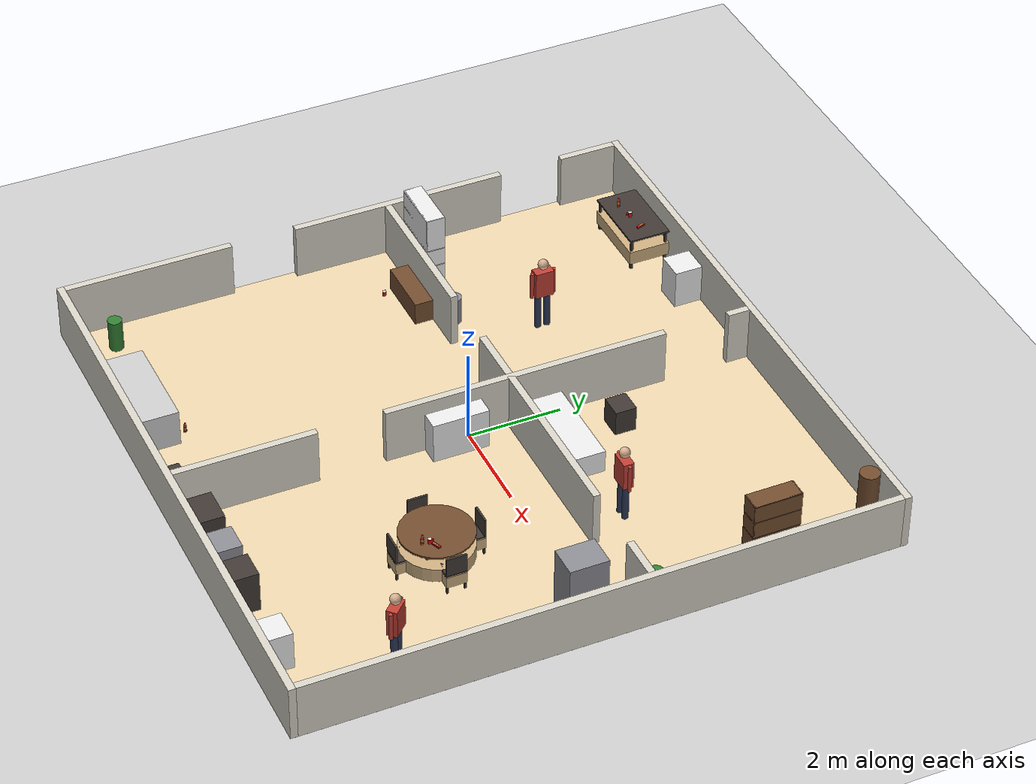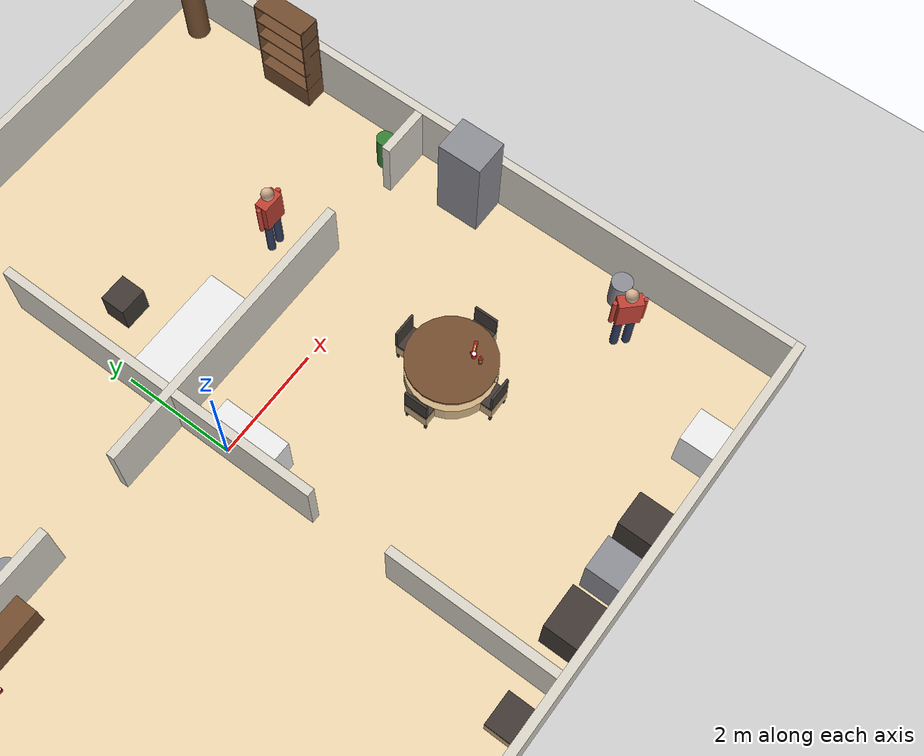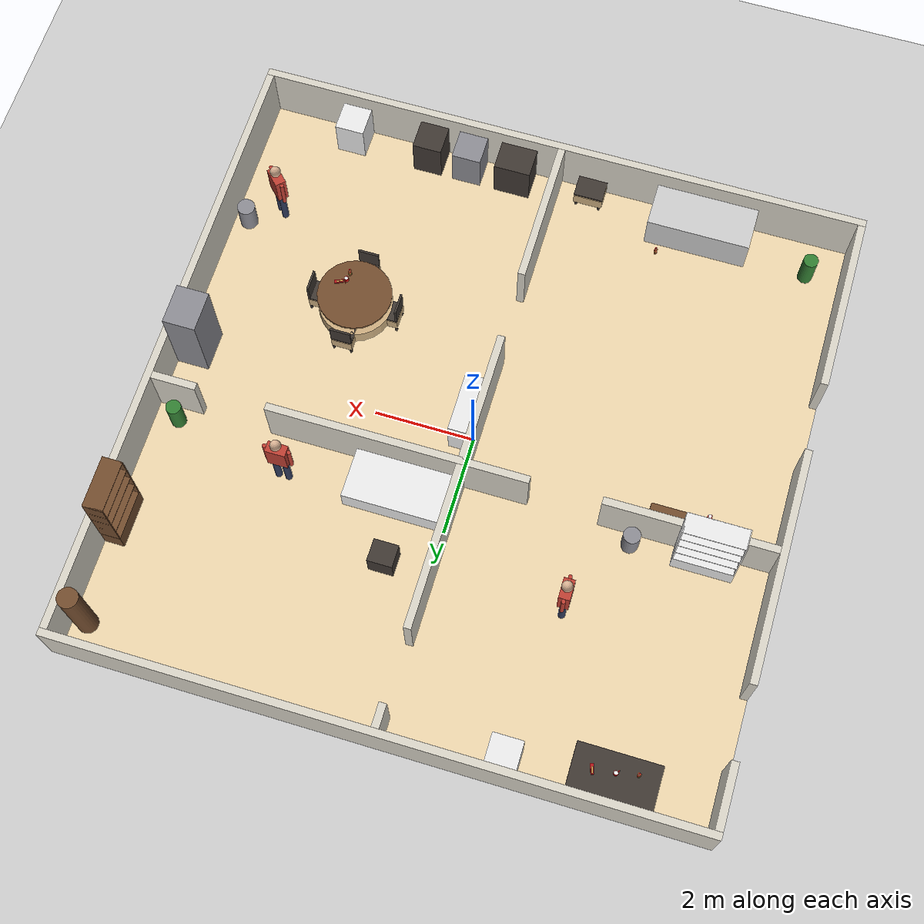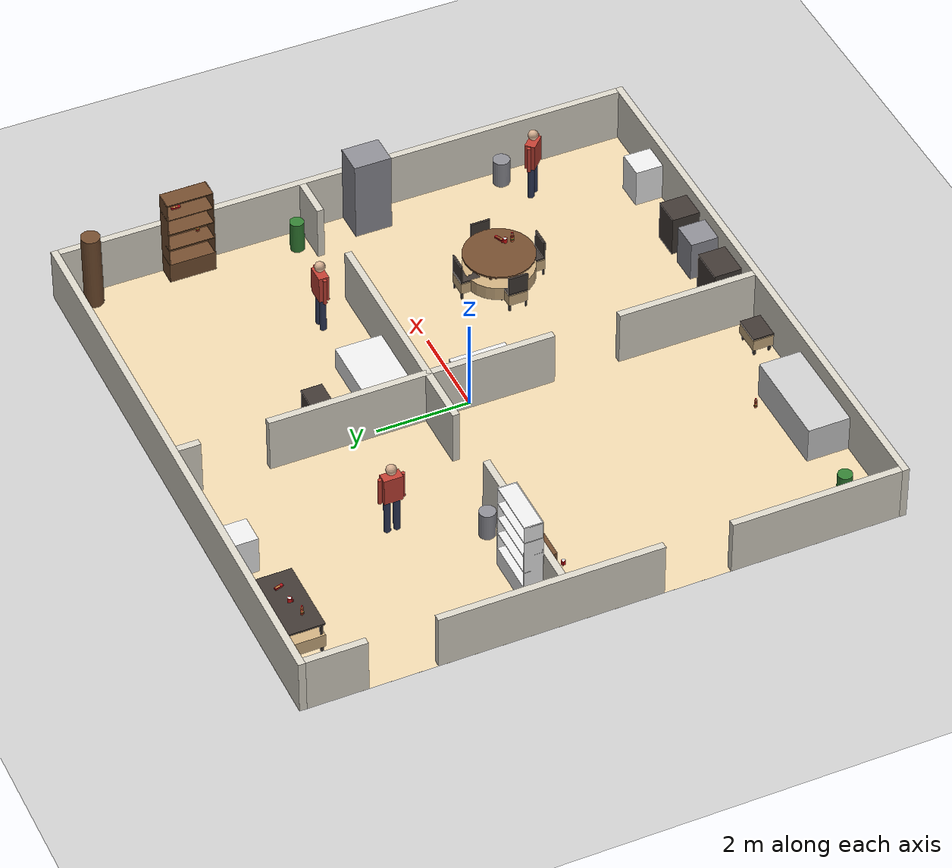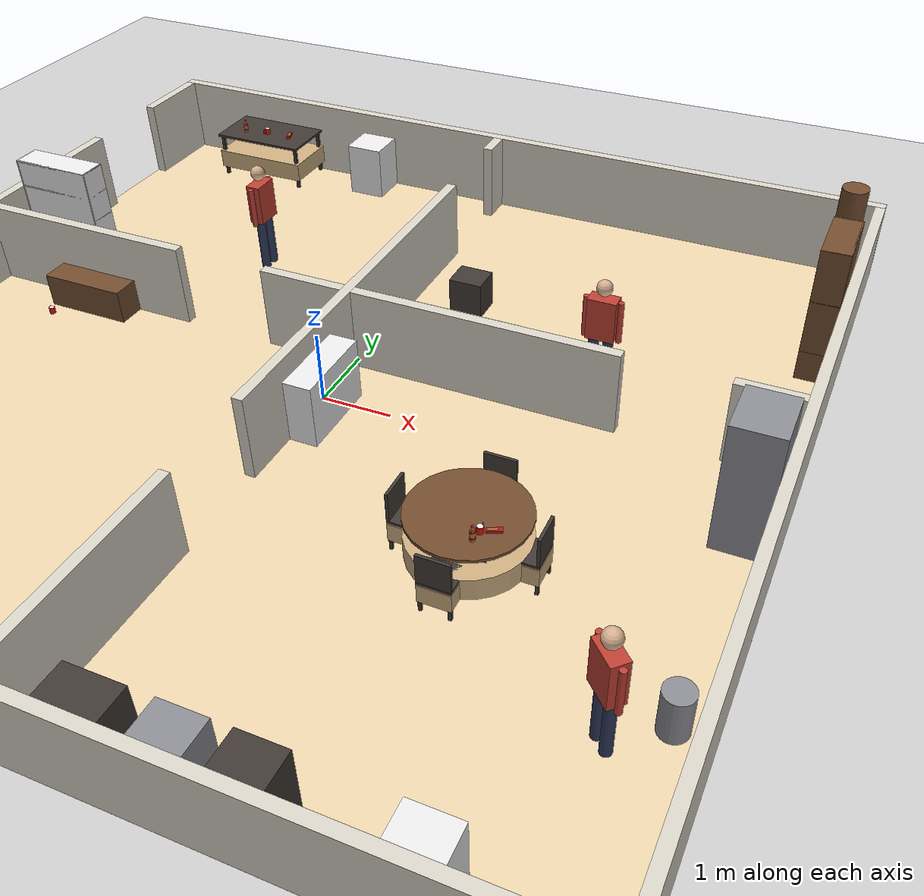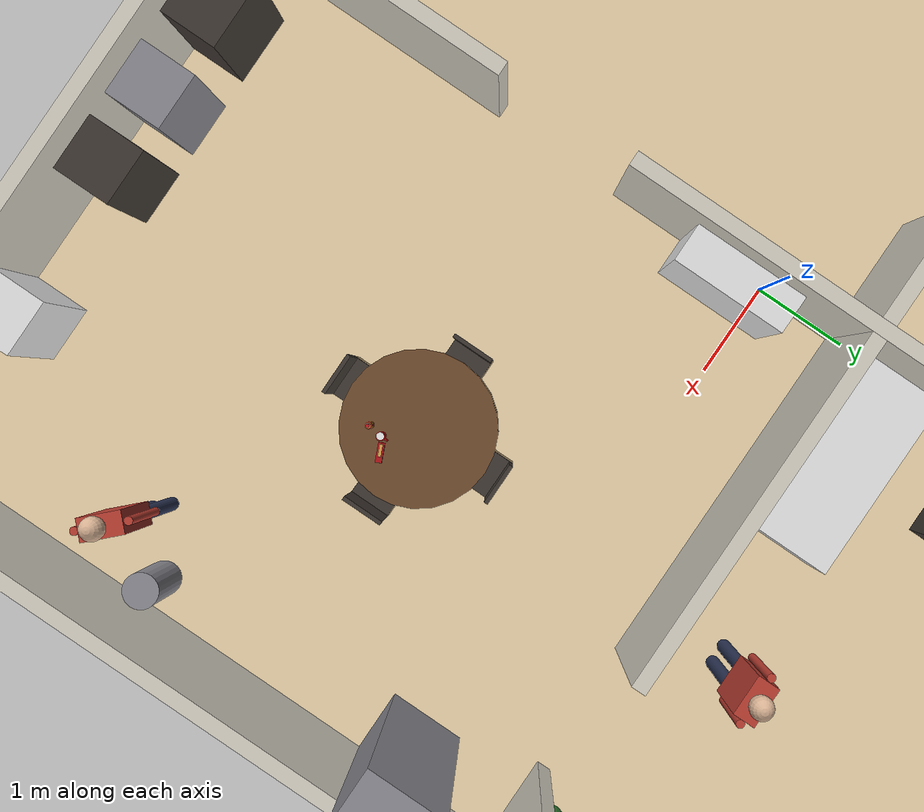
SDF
<?xml version="1.0"?>
<sdf version="1.6">
  <world name="robocup_casa">
    <include><uri>model://sun</uri></include>
    <include><uri>model://ground_plane</uri></include>
    <physics type="ode">
      <max_step_size>0.001</max_step_size>
      <real_time_factor>1.0</real_time_factor>
      <real_time_update_rate>1000</real_time_update_rate>
    </physics>
    <scene><shadows>false</shadows></scene>
    <gui><camera name="user_camera">
      <pose>0.00 -14.11 18.3 0 0.95 1.5708</pose></camera></gui>
    <model name="muros">
      <static>true</static>
      <link name="l0"><pose>0.000 -6.225 0.600 0 0 0.0000</pose>
        <collision name="c"><geometry><box><size>12.600 0.150 1.200</size></box></geometry></collision>
        <visual name="v"><geometry><box><size>12.600 0.150 1.200</size></box></geometry><material><ambient>0.85 0.83 0.78 1</ambient><diffuse>0.85 0.83 0.78 1</diffuse></material></visual>
      </link>
      <link name="l1"><pose>0.000 6.225 0.600 0 0 0.0000</pose>
        <collision name="c"><geometry><box><size>12.600 0.150 1.200</size></box></geometry></collision>
        <visual name="v"><geometry><box><size>12.600 0.150 1.200</size></box></geometry><material><ambient>0.85 0.83 0.78 1</ambient><diffuse>0.85 0.83 0.78 1</diffuse></material></visual>
      </link>
      <link name="l2"><pose>6.225 0.000 0.600 0 0 0.0000</pose>
        <collision name="c"><geometry><box><size>0.150 12.300 1.200</size></box></geometry></collision>
        <visual name="v"><geometry><box><size>0.150 12.300 1.200</size></box></geometry><material><ambient>0.85 0.83 0.78 1</ambient><diffuse>0.85 0.83 0.78 1</diffuse></material></visual>
      </link>
      <link name="l3"><pose>-6.225 -4.356 0.600 0 0 0.0000</pose>
        <collision name="c"><geometry><box><size>0.150 3.588 1.200</size></box></geometry></collision>
        <visual name="v"><geometry><box><size>0.150 3.588 1.200</size></box></geometry><material><ambient>0.85 0.83 0.78 1</ambient><diffuse>0.85 0.83 0.78 1</diffuse></material></visual>
      </link>
      <link name="l4"><pose>-6.225 1.169 0.600 0 0 0.0000</pose>
        <collision name="c"><geometry><box><size>0.150 4.662 1.200</size></box></geometry></collision>
        <visual name="v"><geometry><box><size>0.150 4.662 1.200</size></box></geometry><material><ambient>0.85 0.83 0.78 1</ambient><diffuse>0.85 0.83 0.78 1</diffuse></material></visual>
      </link>
      <link name="l5"><pose>-6.225 5.525 0.600 0 0 0.0000</pose>
        <collision name="c"><geometry><box><size>0.150 1.250 1.200</size></box></geometry></collision>
        <visual name="v"><geometry><box><size>0.150 1.250 1.200</size></box></geometry><material><ambient>0.85 0.83 0.78 1</ambient><diffuse>0.85 0.83 0.78 1</diffuse></material></visual>
      </link>
      <link name="l6"><pose>-0.035 -4.664 0.600 0 0 0.0000</pose>
        <collision name="c"><geometry><box><size>0.150 2.972 1.200</size></box></geometry></collision>
        <visual name="v"><geometry><box><size>0.150 2.972 1.200</size></box></geometry><material><ambient>0.85 0.83 0.78 1</ambient><diffuse>0.85 0.83 0.78 1</diffuse></material></visual>
      </link>
      <link name="l7"><pose>-0.035 1.253 0.600 0 0 0.0000</pose>
        <collision name="c"><geometry><box><size>0.150 6.062 1.200</size></box></geometry></collision>
        <visual name="v"><geometry><box><size>0.150 6.062 1.200</size></box></geometry><material><ambient>0.85 0.83 0.78 1</ambient><diffuse>0.85 0.83 0.78 1</diffuse></material></visual>
      </link>
      <link name="l8"><pose>-0.035 5.917 0.600 0 0 0.0000</pose>
        <collision name="c"><geometry><box><size>0.150 0.466 1.200</size></box></geometry></collision>
        <visual name="v"><geometry><box><size>0.150 0.466 1.200</size></box></geometry><material><ambient>0.85 0.83 0.78 1</ambient><diffuse>0.85 0.83 0.78 1</diffuse></material></visual>
      </link>
      <link name="l9"><pose>-4.461 0.917 0.600 0 0 0.0000</pose>
        <collision name="c"><geometry><box><size>3.378 0.150 1.200</size></box></geometry></collision>
        <visual name="v"><geometry><box><size>3.378 0.150 1.200</size></box></geometry><material><ambient>0.85 0.83 0.78 1</ambient><diffuse>0.85 0.83 0.78 1</diffuse></material></visual>
      </link>
      <link name="l10"><pose>1.239 0.917 0.600 0 0 0.0000</pose>
        <collision name="c"><geometry><box><size>5.222 0.150 1.200</size></box></geometry></collision>
        <visual name="v"><geometry><box><size>5.222 0.150 1.200</size></box></geometry><material><ambient>0.85 0.83 0.78 1</ambient><diffuse>0.85 0.83 0.78 1</diffuse></material></visual>
      </link>
      <link name="l11"><pose>5.700 0.917 0.600 0 0 0.0000</pose>
        <collision name="c"><geometry><box><size>0.900 0.150 1.200</size></box></geometry></collision>
        <visual name="v"><geometry><box><size>0.900 0.150 1.200</size></box></geometry><material><ambient>0.85 0.83 0.78 1</ambient><diffuse>0.85 0.83 0.78 1</diffuse></material></visual>
      </link>
    </model>
    <model name="piso_casa">
      <static>true</static>
      <link name="l"><pose>0.000 0.000 0.0005 0 0 0</pose>
        <visual name="v"><geometry><box><size>12.6 12.6 0.001</size></box></geometry><material><ambient>0.93 0.84 0.68 1</ambient><diffuse>0.93 0.84 0.68 1</diffuse></material></visual>
      </link>
    </model>
    <model name="laundry_table">
      <static>true</static>
      <link name="l0"><pose>-4.298 5.700 0.300 0 0 0.0000</pose>
        <collision name="c"><geometry><box><size>1.600 0.900 0.300</size></box></geometry></collision>
        <visual name="v"><geometry><box><size>1.600 0.900 0.300</size></box></geometry><material><ambient>0.80 0.68 0.50 1</ambient><diffuse>0.80 0.68 0.50 1</diffuse></material></visual>
      </link>
      <link name="l1"><pose>-4.298 5.700 0.730 0 0 0.0000</pose>
        <collision name="c"><geometry><box><size>1.600 0.900 0.040</size></box></geometry></collision>
        <visual name="v"><geometry><box><size>1.600 0.900 0.040</size></box></geometry><material><ambient>0.25 0.22 0.20 1</ambient><diffuse>0.25 0.22 0.20 1</diffuse></material></visual>
      </link>
      <link name="l2"><pose>-5.038 5.310 0.355 0 0 0.0000</pose>
        <collision name="c"><geometry><box><size>0.050 0.050 0.710</size></box></geometry></collision>
        <visual name="v"><geometry><box><size>0.050 0.050 0.710</size></box></geometry><material><ambient>0.25 0.22 0.20 1</ambient><diffuse>0.25 0.22 0.20 1</diffuse></material></visual>
      </link>
      <link name="l3"><pose>-5.038 6.090 0.355 0 0 0.0000</pose>
        <collision name="c"><geometry><box><size>0.050 0.050 0.710</size></box></geometry></collision>
        <visual name="v"><geometry><box><size>0.050 0.050 0.710</size></box></geometry><material><ambient>0.25 0.22 0.20 1</ambient><diffuse>0.25 0.22 0.20 1</diffuse></material></visual>
      </link>
      <link name="l4"><pose>-3.558 5.310 0.355 0 0 0.0000</pose>
        <collision name="c"><geometry><box><size>0.050 0.050 0.710</size></box></geometry></collision>
        <visual name="v"><geometry><box><size>0.050 0.050 0.710</size></box></geometry><material><ambient>0.25 0.22 0.20 1</ambient><diffuse>0.25 0.22 0.20 1</diffuse></material></visual>
      </link>
      <link name="l5"><pose>-3.558 6.090 0.355 0 0 0.0000</pose>
        <collision name="c"><geometry><box><size>0.050 0.050 0.710</size></box></geometry></collision>
        <visual name="v"><geometry><box><size>0.050 0.050 0.710</size></box></geometry><material><ambient>0.25 0.22 0.20 1</ambient><diffuse>0.25 0.22 0.20 1</diffuse></material></visual>
      </link>
    </model>
    <model name="washing_machine">
      <static>true</static>
      <link name="l0"><pose>-2.310 5.850 0.425 0 0 0.0000</pose>
        <collision name="c"><geometry><box><size>0.600 0.600 0.850</size></box></geometry></collision>
        <visual name="v"><geometry><box><size>0.600 0.600 0.850</size></box></geometry><material><ambient>0.92 0.92 0.92 1</ambient><diffuse>0.92 0.92 0.92 1</diffuse></material></visual>
      </link>
    </model>
    <model name="shelf">
      <static>true</static>
      <link name="l0"><pose>-4.900 1.192 0.225 0 0 0.0000</pose>
        <collision name="c"><geometry><box><size>1.200 0.400 0.450</size></box></geometry></collision>
        <visual name="v"><geometry><box><size>1.200 0.400 0.450</size></box></geometry><material><ambient>0.92 0.92 0.92 1</ambient><diffuse>0.92 0.92 0.92 1</diffuse></material></visual>
      </link>
      <link name="l1"><pose>-4.900 1.002 1.225 0 0 0.0000</pose>
        <collision name="c"><geometry><box><size>1.200 0.020 1.550</size></box></geometry></collision>
        <visual name="v"><geometry><box><size>1.200 0.020 1.550</size></box></geometry><material><ambient>0.92 0.92 0.92 1</ambient><diffuse>0.92 0.92 0.92 1</diffuse></material></visual>
      </link>
      <link name="l2"><pose>-5.490 1.192 1.225 0 0 0.0000</pose>
        <collision name="c"><geometry><box><size>0.020 0.400 1.550</size></box></geometry></collision>
        <visual name="v"><geometry><box><size>0.020 0.400 1.550</size></box></geometry><material><ambient>0.92 0.92 0.92 1</ambient><diffuse>0.92 0.92 0.92 1</diffuse></material></visual>
      </link>
      <link name="l3"><pose>-4.310 1.192 1.225 0 0 0.0000</pose>
        <collision name="c"><geometry><box><size>0.020 0.400 1.550</size></box></geometry></collision>
        <visual name="v"><geometry><box><size>0.020 0.400 1.550</size></box></geometry><material><ambient>0.92 0.92 0.92 1</ambient><diffuse>0.92 0.92 0.92 1</diffuse></material></visual>
      </link>
      <link name="l4"><pose>-4.900 1.192 0.840 0 0 0.0000</pose>
        <collision name="c"><geometry><box><size>1.200 0.400 0.020</size></box></geometry></collision>
        <visual name="v"><geometry><box><size>1.200 0.400 0.020</size></box></geometry><material><ambient>0.92 0.92 0.92 1</ambient><diffuse>0.92 0.92 0.92 1</diffuse></material></visual>
      </link>
      <link name="l5"><pose>-4.900 1.192 1.240 0 0 0.0000</pose>
        <collision name="c"><geometry><box><size>1.200 0.400 0.020</size></box></geometry></collision>
        <visual name="v"><geometry><box><size>1.200 0.400 0.020</size></box></geometry><material><ambient>0.92 0.92 0.92 1</ambient><diffuse>0.92 0.92 0.92 1</diffuse></material></visual>
      </link>
      <link name="l6"><pose>-4.900 1.192 1.610 0 0 0.0000</pose>
        <collision name="c"><geometry><box><size>1.200 0.400 0.020</size></box></geometry></collision>
        <visual name="v"><geometry><box><size>1.200 0.400 0.020</size></box></geometry><material><ambient>0.92 0.92 0.92 1</ambient><diffuse>0.92 0.92 0.92 1</diffuse></material></visual>
      </link>
      <link name="l7"><pose>-4.900 1.192 1.990 0 0 0.0000</pose>
        <collision name="c"><geometry><box><size>1.200 0.400 0.020</size></box></geometry></collision>
        <visual name="v"><geometry><box><size>1.200 0.400 0.020</size></box></geometry><material><ambient>0.92 0.92 0.92 1</ambient><diffuse>0.92 0.92 0.92 1</diffuse></material></visual>
      </link>
    </model>
    <model name="laundry_trash_bin">
      <static>true</static>
      <link name="l0"><pose>-3.472 1.212 0.300 0 0 0.0000</pose>
        <collision name="c"><geometry><cylinder><radius>0.170</radius><length>0.600</length></cylinder></geometry></collision>
        <visual name="v"><geometry><cylinder><radius>0.170</radius><length>0.600</length></cylinder></geometry><material><ambient>0.55 0.55 0.58 1</ambient><diffuse>0.55 0.55 0.58 1</diffuse></material></visual>
      </link>
    </model>
    <model name="bed">
      <static>true</static>
      <link name="l0"><pose>1.040 1.492 0.250 0 0 0.0000</pose>
        <collision name="c"><geometry><box><size>2.000 1.000 0.500</size></box></geometry></collision>
        <visual name="v"><geometry><box><size>2.000 1.000 0.500</size></box></geometry><material><ambient>0.92 0.92 0.92 1</ambient><diffuse>0.92 0.92 0.92 1</diffuse></material></visual>
      </link>
    </model>
    <model name="bedside_table">
      <static>true</static>
      <link name="l0"><pose>0.910 2.870 0.275 0 0 0.0000</pose>
        <collision name="c"><geometry><box><size>0.500 0.450 0.550</size></box></geometry></collision>
        <visual name="v"><geometry><box><size>0.500 0.450 0.550</size></box></geometry><material><ambient>0.25 0.22 0.20 1</ambient><diffuse>0.25 0.22 0.20 1</diffuse></material></visual>
      </link>
    </model>
    <model name="coat_rack">
      <static>true</static>
      <link name="l0"><pose>5.850 5.600 0.850 0 0 0.0000</pose>
        <collision name="c"><geometry><cylinder><radius>0.200</radius><length>1.700</length></cylinder></geometry></collision>
        <visual name="v"><geometry><cylinder><radius>0.200</radius><length>1.700</length></cylinder></geometry><material><ambient>0.45 0.30 0.18 1</ambient><diffuse>0.45 0.30 0.18 1</diffuse></material></visual>
      </link>
    </model>
    <model name="bookshelf">
      <static>true</static>
      <link name="l0"><pose>5.950 3.500 0.225 0 0 0.0000</pose>
        <collision name="c"><geometry><box><size>0.400 1.000 0.450</size></box></geometry></collision>
        <visual name="v"><geometry><box><size>0.400 1.000 0.450</size></box></geometry><material><ambient>0.45 0.30 0.18 1</ambient><diffuse>0.45 0.30 0.18 1</diffuse></material></visual>
      </link>
      <link name="l1"><pose>6.140 3.500 1.225 0 0 0.0000</pose>
        <collision name="c"><geometry><box><size>0.020 1.000 1.550</size></box></geometry></collision>
        <visual name="v"><geometry><box><size>0.020 1.000 1.550</size></box></geometry><material><ambient>0.45 0.30 0.18 1</ambient><diffuse>0.45 0.30 0.18 1</diffuse></material></visual>
      </link>
      <link name="l2"><pose>5.950 3.010 1.225 0 0 0.0000</pose>
        <collision name="c"><geometry><box><size>0.400 0.020 1.550</size></box></geometry></collision>
        <visual name="v"><geometry><box><size>0.400 0.020 1.550</size></box></geometry><material><ambient>0.45 0.30 0.18 1</ambient><diffuse>0.45 0.30 0.18 1</diffuse></material></visual>
      </link>
      <link name="l3"><pose>5.950 3.990 1.225 0 0 0.0000</pose>
        <collision name="c"><geometry><box><size>0.400 0.020 1.550</size></box></geometry></collision>
        <visual name="v"><geometry><box><size>0.400 0.020 1.550</size></box></geometry><material><ambient>0.45 0.30 0.18 1</ambient><diffuse>0.45 0.30 0.18 1</diffuse></material></visual>
      </link>
      <link name="l4"><pose>5.950 3.500 0.840 0 0 0.0000</pose>
        <collision name="c"><geometry><box><size>0.400 1.000 0.020</size></box></geometry></collision>
        <visual name="v"><geometry><box><size>0.400 1.000 0.020</size></box></geometry><material><ambient>0.45 0.30 0.18 1</ambient><diffuse>0.45 0.30 0.18 1</diffuse></material></visual>
      </link>
      <link name="l5"><pose>5.950 3.500 1.240 0 0 0.0000</pose>
        <collision name="c"><geometry><box><size>0.400 1.000 0.020</size></box></geometry></collision>
        <visual name="v"><geometry><box><size>0.400 1.000 0.020</size></box></geometry><material><ambient>0.45 0.30 0.18 1</ambient><diffuse>0.45 0.30 0.18 1</diffuse></material></visual>
      </link>
      <link name="l6"><pose>5.950 3.500 1.610 0 0 0.0000</pose>
        <collision name="c"><geometry><box><size>0.400 1.000 0.020</size></box></geometry></collision>
        <visual name="v"><geometry><box><size>0.400 1.000 0.020</size></box></geometry><material><ambient>0.45 0.30 0.18 1</ambient><diffuse>0.45 0.30 0.18 1</diffuse></material></visual>
      </link>
      <link name="l7"><pose>5.950 3.500 1.990 0 0 0.0000</pose>
        <collision name="c"><geometry><box><size>0.400 1.000 0.020</size></box></geometry></collision>
        <visual name="v"><geometry><box><size>0.400 1.000 0.020</size></box></geometry><material><ambient>0.45 0.30 0.18 1</ambient><diffuse>0.45 0.30 0.18 1</diffuse></material></visual>
      </link>
    </model>
    <model name="planta_bedroom">
      <static>true</static>
      <link name="l0"><pose>5.670 1.262 0.350 0 0 0.0000</pose>
        <collision name="c"><geometry><cylinder><radius>0.150</radius><length>0.700</length></cylinder></geometry></collision>
        <visual name="v"><geometry><cylinder><radius>0.150</radius><length>0.700</length></cylinder></geometry><material><ambient>0.20 0.50 0.20 1</ambient><diffuse>0.20 0.50 0.20 1</diffuse></material></visual>
      </link>
    </model>
    <model name="tv_stand">
      <static>true</static>
      <link name="l0"><pose>-4.312 0.642 0.250 0 0 0.0000</pose>
        <collision name="c"><geometry><box><size>1.300 0.400 0.500</size></box></geometry></collision>
        <visual name="v"><geometry><box><size>1.300 0.400 0.500</size></box></geometry><material><ambient>0.45 0.30 0.18 1</ambient><diffuse>0.45 0.30 0.18 1</diffuse></material></visual>
      </link>
    </model>
    <model name="sofa">
      <static>true</static>
      <link name="l0"><pose>-3.150 -5.700 0.400 0 0 0.0000</pose>
        <collision name="c"><geometry><box><size>2.100 0.900 0.800</size></box></geometry></collision>
        <visual name="v"><geometry><box><size>2.100 0.900 0.800</size></box></geometry><material><ambient>0.80 0.80 0.80 1</ambient><diffuse>0.80 0.80 0.80 1</diffuse></material></visual>
      </link>
    </model>
    <model name="coffee_table">
      <static>true</static>
      <link name="l0"><pose>-0.770 -5.880 0.275 0 0 0.0000</pose>
        <collision name="c"><geometry><box><size>0.600 0.450 0.250</size></box></geometry></collision>
        <visual name="v"><geometry><box><size>0.600 0.450 0.250</size></box></geometry><material><ambient>0.80 0.68 0.50 1</ambient><diffuse>0.80 0.68 0.50 1</diffuse></material></visual>
      </link>
      <link name="l1"><pose>-0.770 -5.880 0.430 0 0 0.0000</pose>
        <collision name="c"><geometry><box><size>0.600 0.450 0.040</size></box></geometry></collision>
        <visual name="v"><geometry><box><size>0.600 0.450 0.040</size></box></geometry><material><ambient>0.25 0.22 0.20 1</ambient><diffuse>0.25 0.22 0.20 1</diffuse></material></visual>
      </link>
      <link name="l2"><pose>-1.010 -6.045 0.205 0 0 0.0000</pose>
        <collision name="c"><geometry><box><size>0.050 0.050 0.410</size></box></geometry></collision>
        <visual name="v"><geometry><box><size>0.050 0.050 0.410</size></box></geometry><material><ambient>0.25 0.22 0.20 1</ambient><diffuse>0.25 0.22 0.20 1</diffuse></material></visual>
      </link>
      <link name="l3"><pose>-1.010 -5.715 0.205 0 0 0.0000</pose>
        <collision name="c"><geometry><box><size>0.050 0.050 0.410</size></box></geometry></collision>
        <visual name="v"><geometry><box><size>0.050 0.050 0.410</size></box></geometry><material><ambient>0.25 0.22 0.20 1</ambient><diffuse>0.25 0.22 0.20 1</diffuse></material></visual>
      </link>
      <link name="l4"><pose>-0.530 -6.045 0.205 0 0 0.0000</pose>
        <collision name="c"><geometry><box><size>0.050 0.050 0.410</size></box></geometry></collision>
        <visual name="v"><geometry><box><size>0.050 0.050 0.410</size></box></geometry><material><ambient>0.25 0.22 0.20 1</ambient><diffuse>0.25 0.22 0.20 1</diffuse></material></visual>
      </link>
      <link name="l5"><pose>-0.530 -5.715 0.205 0 0 0.0000</pose>
        <collision name="c"><geometry><box><size>0.050 0.050 0.410</size></box></geometry></collision>
        <visual name="v"><geometry><box><size>0.050 0.050 0.410</size></box></geometry><material><ambient>0.25 0.22 0.20 1</ambient><diffuse>0.25 0.22 0.20 1</diffuse></material></visual>
      </link>
    </model>
    <model name="planta_living">
      <static>true</static>
      <link name="l0"><pose>-5.460 -5.390 0.350 0 0 0.0000</pose>
        <collision name="c"><geometry><cylinder><radius>0.150</radius><length>0.700</length></cylinder></geometry></collision>
        <visual name="v"><geometry><cylinder><radius>0.150</radius><length>0.700</length></cylinder></geometry><material><ambient>0.20 0.50 0.20 1</ambient><diffuse>0.20 0.50 0.20 1</diffuse></material></visual>
      </link>
    </model>
    <model name="cabinet">
      <static>true</static>
      <link name="l0"><pose>0.240 -0.350 0.450 0 0 0.0000</pose>
        <collision name="c"><geometry><box><size>0.400 1.200 0.900</size></box></geometry></collision>
        <visual name="v"><geometry><box><size>0.400 1.200 0.900</size></box></geometry><material><ambient>0.92 0.92 0.92 1</ambient><diffuse>0.92 0.92 0.92 1</diffuse></material></visual>
      </link>
    </model>
    <model name="refrigerator">
      <static>true</static>
      <link name="l0"><pose>5.825 -0.350 0.900 0 0 0.0000</pose>
        <collision name="c"><geometry><box><size>0.650 0.800 1.800</size></box></geometry></collision>
        <visual name="v"><geometry><box><size>0.650 0.800 1.800</size></box></geometry><material><ambient>0.55 0.55 0.58 1</ambient><diffuse>0.55 0.55 0.58 1</diffuse></material></visual>
      </link>
    </model>
    <model name="kitchen_trash_bin">
      <static>true</static>
      <link name="l0"><pose>5.850 -3.360 0.300 0 0 0.0000</pose>
        <collision name="c"><geometry><cylinder><radius>0.180</radius><length>0.600</length></cylinder></geometry></collision>
        <visual name="v"><geometry><cylinder><radius>0.180</radius><length>0.600</length></cylinder></geometry><material><ambient>0.55 0.55 0.58 1</ambient><diffuse>0.55 0.55 0.58 1</diffuse></material></visual>
      </link>
    </model>
    <model name="dinner_table">
      <static>true</static>
      <link name="l0"><pose>3.066 -2.030 0.300 0 0 0.0000</pose>
        <collision name="c"><geometry><cylinder><radius>0.750</radius><length>0.300</length></cylinder></geometry></collision>
        <visual name="v"><geometry><cylinder><radius>0.750</radius><length>0.300</length></cylinder></geometry><material><ambient>0.80 0.68 0.50 1</ambient><diffuse>0.80 0.68 0.50 1</diffuse></material></visual>
      </link>
      <link name="l1"><pose>3.066 -2.030 0.730 0 0 0.0000</pose>
        <collision name="c"><geometry><cylinder><radius>0.750</radius><length>0.040</length></cylinder></geometry></collision>
        <visual name="v"><geometry><cylinder><radius>0.750</radius><length>0.040</length></cylinder></geometry><material><ambient>0.45 0.30 0.18 1</ambient><diffuse>0.45 0.30 0.18 1</diffuse></material></visual>
      </link>
      <link name="l2"><pose>2.721 -2.375 0.355 0 0 0.0000</pose>
        <collision name="c"><geometry><box><size>0.050 0.050 0.710</size></box></geometry></collision>
        <visual name="v"><geometry><box><size>0.050 0.050 0.710</size></box></geometry><material><ambient>0.45 0.30 0.18 1</ambient><diffuse>0.45 0.30 0.18 1</diffuse></material></visual>
      </link>
      <link name="l3"><pose>2.721 -1.685 0.355 0 0 0.0000</pose>
        <collision name="c"><geometry><box><size>0.050 0.050 0.710</size></box></geometry></collision>
        <visual name="v"><geometry><box><size>0.050 0.050 0.710</size></box></geometry><material><ambient>0.45 0.30 0.18 1</ambient><diffuse>0.45 0.30 0.18 1</diffuse></material></visual>
      </link>
      <link name="l4"><pose>3.411 -2.375 0.355 0 0 0.0000</pose>
        <collision name="c"><geometry><box><size>0.050 0.050 0.710</size></box></geometry></collision>
        <visual name="v"><geometry><box><size>0.050 0.050 0.710</size></box></geometry><material><ambient>0.45 0.30 0.18 1</ambient><diffuse>0.45 0.30 0.18 1</diffuse></material></visual>
      </link>
      <link name="l5"><pose>3.411 -1.685 0.355 0 0 0.0000</pose>
        <collision name="c"><geometry><box><size>0.050 0.050 0.710</size></box></geometry></collision>
        <visual name="v"><geometry><box><size>0.050 0.050 0.710</size></box></geometry><material><ambient>0.45 0.30 0.18 1</ambient><diffuse>0.45 0.30 0.18 1</diffuse></material></visual>
      </link>
    </model>
    <model name="counter">
      <static>true</static>
      <link name="l0"><pose>0.840 -5.850 0.450 0 0 0.0000</pose>
        <collision name="c"><geometry><box><size>0.750 0.600 0.900</size></box></geometry></collision>
        <visual name="v"><geometry><box><size>0.750 0.600 0.900</size></box></geometry><material><ambient>0.25 0.22 0.20 1</ambient><diffuse>0.25 0.22 0.20 1</diffuse></material></visual>
      </link>
    </model>
    <model name="sink">
      <static>true</static>
      <link name="l0"><pose>1.820 -5.850 0.450 0 0 0.0000</pose>
        <collision name="c"><geometry><box><size>0.600 0.600 0.900</size></box></geometry></collision>
        <visual name="v"><geometry><box><size>0.600 0.600 0.900</size></box></geometry><material><ambient>0.55 0.55 0.58 1</ambient><diffuse>0.55 0.55 0.58 1</diffuse></material></visual>
      </link>
    </model>
    <model name="cooking_table">
      <static>true</static>
      <link name="l0"><pose>2.660 -5.850 0.450 0 0 0.0000</pose>
        <collision name="c"><geometry><box><size>0.600 0.600 0.900</size></box></geometry></collision>
        <visual name="v"><geometry><box><size>0.600 0.600 0.900</size></box></geometry><material><ambient>0.25 0.22 0.20 1</ambient><diffuse>0.25 0.22 0.20 1</diffuse></material></visual>
      </link>
    </model>
    <model name="dishwasher">
      <static>true</static>
      <link name="l0"><pose>4.340 -5.850 0.425 0 0 0.0000</pose>
        <collision name="c"><geometry><box><size>0.600 0.600 0.850</size></box></geometry></collision>
        <visual name="v"><geometry><box><size>0.600 0.600 0.850</size></box></geometry><material><ambient>0.92 0.92 0.92 1</ambient><diffuse>0.92 0.92 0.92 1</diffuse></material></visual>
      </link>
    </model>
    <model name="silla_n">
      <static>true</static>
      <link name="l0"><pose>3.066 -1.310 0.275 0 0 -1.5708</pose>
        <collision name="c"><geometry><box><size>0.420 0.420 0.250</size></box></geometry></collision>
        <visual name="v"><geometry><box><size>0.420 0.420 0.250</size></box></geometry><material><ambient>0.80 0.68 0.50 1</ambient><diffuse>0.80 0.68 0.50 1</diffuse></material></visual>
      </link>
      <link name="l1"><pose>3.066 -1.310 0.430 0 0 -1.5708</pose>
        <collision name="c"><geometry><box><size>0.420 0.420 0.040</size></box></geometry></collision>
        <visual name="v"><geometry><box><size>0.420 0.420 0.040</size></box></geometry><material><ambient>0.25 0.22 0.20 1</ambient><diffuse>0.25 0.22 0.20 1</diffuse></material></visual>
      </link>
      <link name="l2"><pose>2.886 -1.130 0.205 0 0 -1.5708</pose>
        <collision name="c"><geometry><box><size>0.040 0.040 0.410</size></box></geometry></collision>
        <visual name="v"><geometry><box><size>0.040 0.040 0.410</size></box></geometry><material><ambient>0.25 0.22 0.20 1</ambient><diffuse>0.25 0.22 0.20 1</diffuse></material></visual>
      </link>
      <link name="l3"><pose>3.246 -1.130 0.205 0 0 -1.5708</pose>
        <collision name="c"><geometry><box><size>0.040 0.040 0.410</size></box></geometry></collision>
        <visual name="v"><geometry><box><size>0.040 0.040 0.410</size></box></geometry><material><ambient>0.25 0.22 0.20 1</ambient><diffuse>0.25 0.22 0.20 1</diffuse></material></visual>
      </link>
      <link name="l4"><pose>2.886 -1.490 0.205 0 0 -1.5708</pose>
        <collision name="c"><geometry><box><size>0.040 0.040 0.410</size></box></geometry></collision>
        <visual name="v"><geometry><box><size>0.040 0.040 0.410</size></box></geometry><material><ambient>0.25 0.22 0.20 1</ambient><diffuse>0.25 0.22 0.20 1</diffuse></material></visual>
      </link>
      <link name="l5"><pose>3.246 -1.490 0.205 0 0 -1.5708</pose>
        <collision name="c"><geometry><box><size>0.040 0.040 0.410</size></box></geometry></collision>
        <visual name="v"><geometry><box><size>0.040 0.040 0.410</size></box></geometry><material><ambient>0.25 0.22 0.20 1</ambient><diffuse>0.25 0.22 0.20 1</diffuse></material></visual>
      </link>
      <link name="l6"><pose>3.066 -1.120 0.650 0 0 -1.5708</pose>
        <collision name="c"><geometry><box><size>0.040 0.420 0.400</size></box></geometry></collision>
        <visual name="v"><geometry><box><size>0.040 0.420 0.400</size></box></geometry><material><ambient>0.25 0.22 0.20 1</ambient><diffuse>0.25 0.22 0.20 1</diffuse></material></visual>
      </link>
    </model>
    <model name="silla_s">
      <static>true</static>
      <link name="l0"><pose>3.066 -2.750 0.275 0 0 1.5708</pose>
        <collision name="c"><geometry><box><size>0.420 0.420 0.250</size></box></geometry></collision>
        <visual name="v"><geometry><box><size>0.420 0.420 0.250</size></box></geometry><material><ambient>0.80 0.68 0.50 1</ambient><diffuse>0.80 0.68 0.50 1</diffuse></material></visual>
      </link>
      <link name="l1"><pose>3.066 -2.750 0.430 0 0 1.5708</pose>
        <collision name="c"><geometry><box><size>0.420 0.420 0.040</size></box></geometry></collision>
        <visual name="v"><geometry><box><size>0.420 0.420 0.040</size></box></geometry><material><ambient>0.25 0.22 0.20 1</ambient><diffuse>0.25 0.22 0.20 1</diffuse></material></visual>
      </link>
      <link name="l2"><pose>3.246 -2.930 0.205 0 0 1.5708</pose>
        <collision name="c"><geometry><box><size>0.040 0.040 0.410</size></box></geometry></collision>
        <visual name="v"><geometry><box><size>0.040 0.040 0.410</size></box></geometry><material><ambient>0.25 0.22 0.20 1</ambient><diffuse>0.25 0.22 0.20 1</diffuse></material></visual>
      </link>
      <link name="l3"><pose>2.886 -2.930 0.205 0 0 1.5708</pose>
        <collision name="c"><geometry><box><size>0.040 0.040 0.410</size></box></geometry></collision>
        <visual name="v"><geometry><box><size>0.040 0.040 0.410</size></box></geometry><material><ambient>0.25 0.22 0.20 1</ambient><diffuse>0.25 0.22 0.20 1</diffuse></material></visual>
      </link>
      <link name="l4"><pose>3.246 -2.570 0.205 0 0 1.5708</pose>
        <collision name="c"><geometry><box><size>0.040 0.040 0.410</size></box></geometry></collision>
        <visual name="v"><geometry><box><size>0.040 0.040 0.410</size></box></geometry><material><ambient>0.25 0.22 0.20 1</ambient><diffuse>0.25 0.22 0.20 1</diffuse></material></visual>
      </link>
      <link name="l5"><pose>2.886 -2.570 0.205 0 0 1.5708</pose>
        <collision name="c"><geometry><box><size>0.040 0.040 0.410</size></box></geometry></collision>
        <visual name="v"><geometry><box><size>0.040 0.040 0.410</size></box></geometry><material><ambient>0.25 0.22 0.20 1</ambient><diffuse>0.25 0.22 0.20 1</diffuse></material></visual>
      </link>
      <link name="l6"><pose>3.066 -2.940 0.650 0 0 1.5708</pose>
        <collision name="c"><geometry><box><size>0.040 0.420 0.400</size></box></geometry></collision>
        <visual name="v"><geometry><box><size>0.040 0.420 0.400</size></box></geometry><material><ambient>0.25 0.22 0.20 1</ambient><diffuse>0.25 0.22 0.20 1</diffuse></material></visual>
      </link>
    </model>
    <model name="silla_o">
      <static>true</static>
      <link name="l0"><pose>2.346 -2.030 0.275 0 0 0.0000</pose>
        <collision name="c"><geometry><box><size>0.420 0.420 0.250</size></box></geometry></collision>
        <visual name="v"><geometry><box><size>0.420 0.420 0.250</size></box></geometry><material><ambient>0.80 0.68 0.50 1</ambient><diffuse>0.80 0.68 0.50 1</diffuse></material></visual>
      </link>
      <link name="l1"><pose>2.346 -2.030 0.430 0 0 0.0000</pose>
        <collision name="c"><geometry><box><size>0.420 0.420 0.040</size></box></geometry></collision>
        <visual name="v"><geometry><box><size>0.420 0.420 0.040</size></box></geometry><material><ambient>0.25 0.22 0.20 1</ambient><diffuse>0.25 0.22 0.20 1</diffuse></material></visual>
      </link>
      <link name="l2"><pose>2.166 -2.210 0.205 0 0 0.0000</pose>
        <collision name="c"><geometry><box><size>0.040 0.040 0.410</size></box></geometry></collision>
        <visual name="v"><geometry><box><size>0.040 0.040 0.410</size></box></geometry><material><ambient>0.25 0.22 0.20 1</ambient><diffuse>0.25 0.22 0.20 1</diffuse></material></visual>
      </link>
      <link name="l3"><pose>2.166 -1.850 0.205 0 0 0.0000</pose>
        <collision name="c"><geometry><box><size>0.040 0.040 0.410</size></box></geometry></collision>
        <visual name="v"><geometry><box><size>0.040 0.040 0.410</size></box></geometry><material><ambient>0.25 0.22 0.20 1</ambient><diffuse>0.25 0.22 0.20 1</diffuse></material></visual>
      </link>
      <link name="l4"><pose>2.526 -2.210 0.205 0 0 0.0000</pose>
        <collision name="c"><geometry><box><size>0.040 0.040 0.410</size></box></geometry></collision>
        <visual name="v"><geometry><box><size>0.040 0.040 0.410</size></box></geometry><material><ambient>0.25 0.22 0.20 1</ambient><diffuse>0.25 0.22 0.20 1</diffuse></material></visual>
      </link>
      <link name="l5"><pose>2.526 -1.850 0.205 0 0 0.0000</pose>
        <collision name="c"><geometry><box><size>0.040 0.040 0.410</size></box></geometry></collision>
        <visual name="v"><geometry><box><size>0.040 0.040 0.410</size></box></geometry><material><ambient>0.25 0.22 0.20 1</ambient><diffuse>0.25 0.22 0.20 1</diffuse></material></visual>
      </link>
      <link name="l6"><pose>2.156 -2.030 0.650 0 0 0.0000</pose>
        <collision name="c"><geometry><box><size>0.040 0.420 0.400</size></box></geometry></collision>
        <visual name="v"><geometry><box><size>0.040 0.420 0.400</size></box></geometry><material><ambient>0.25 0.22 0.20 1</ambient><diffuse>0.25 0.22 0.20 1</diffuse></material></visual>
      </link>
    </model>
    <model name="silla_e">
      <static>true</static>
      <link name="l0"><pose>3.786 -2.030 0.275 0 0 3.1416</pose>
        <collision name="c"><geometry><box><size>0.420 0.420 0.250</size></box></geometry></collision>
        <visual name="v"><geometry><box><size>0.420 0.420 0.250</size></box></geometry><material><ambient>0.80 0.68 0.50 1</ambient><diffuse>0.80 0.68 0.50 1</diffuse></material></visual>
      </link>
      <link name="l1"><pose>3.786 -2.030 0.430 0 0 3.1416</pose>
        <collision name="c"><geometry><box><size>0.420 0.420 0.040</size></box></geometry></collision>
        <visual name="v"><geometry><box><size>0.420 0.420 0.040</size></box></geometry><material><ambient>0.25 0.22 0.20 1</ambient><diffuse>0.25 0.22 0.20 1</diffuse></material></visual>
      </link>
      <link name="l2"><pose>3.966 -1.850 0.205 0 0 3.1416</pose>
        <collision name="c"><geometry><box><size>0.040 0.040 0.410</size></box></geometry></collision>
        <visual name="v"><geometry><box><size>0.040 0.040 0.410</size></box></geometry><material><ambient>0.25 0.22 0.20 1</ambient><diffuse>0.25 0.22 0.20 1</diffuse></material></visual>
      </link>
      <link name="l3"><pose>3.966 -2.210 0.205 0 0 3.1416</pose>
        <collision name="c"><geometry><box><size>0.040 0.040 0.410</size></box></geometry></collision>
        <visual name="v"><geometry><box><size>0.040 0.040 0.410</size></box></geometry><material><ambient>0.25 0.22 0.20 1</ambient><diffuse>0.25 0.22 0.20 1</diffuse></material></visual>
      </link>
      <link name="l4"><pose>3.606 -1.850 0.205 0 0 3.1416</pose>
        <collision name="c"><geometry><box><size>0.040 0.040 0.410</size></box></geometry></collision>
        <visual name="v"><geometry><box><size>0.040 0.040 0.410</size></box></geometry><material><ambient>0.25 0.22 0.20 1</ambient><diffuse>0.25 0.22 0.20 1</diffuse></material></visual>
      </link>
      <link name="l5"><pose>3.606 -2.210 0.205 0 0 3.1416</pose>
        <collision name="c"><geometry><box><size>0.040 0.040 0.410</size></box></geometry></collision>
        <visual name="v"><geometry><box><size>0.040 0.040 0.410</size></box></geometry><material><ambient>0.25 0.22 0.20 1</ambient><diffuse>0.25 0.22 0.20 1</diffuse></material></visual>
      </link>
      <link name="l6"><pose>3.976 -2.030 0.650 0 0 3.1416</pose>
        <collision name="c"><geometry><box><size>0.040 0.420 0.400</size></box></geometry></collision>
        <visual name="v"><geometry><box><size>0.040 0.420 0.400</size></box></geometry><material><ambient>0.25 0.22 0.20 1</ambient><diffuse>0.25 0.22 0.20 1</diffuse></material></visual>
      </link>
    </model>
    <model name="botella_laundry">
      <pose>-4.698 5.550 0.751 0 0 1.571</pose>
      <link name="link">
        <inertial><pose>0 0 0.1100 0 0 0</pose><mass>0.55</mass><inertia><ixx>2.368e-03</ixx><iyy>2.368e-03</iyy><izz>2.995e-04</izz><ixy>0</ixy><ixz>0</ixz><iyz>0</iyz></inertia></inertial>
        <collision name="c"><pose>0 0 0.1100 0 0 0</pose><geometry><cylinder><radius>0.0330</radius><length>0.2200</length></cylinder></geometry><surface><friction><ode><mu>1.0</mu><mu2>1.0</mu2></ode></friction></surface></collision>
        <visual name="v0"><pose>0 0 0.075 0 0 0</pose><geometry><cylinder><radius>0.0330</radius><length>0.1500</length></cylinder></geometry><transparency>0</transparency><material><ambient>0.86 0.40 0.22 1</ambient><diffuse>0.86 0.40 0.22 1</diffuse></material></visual>
        <visual name="v1"><pose>0 0 0.16 0 0 0</pose><geometry><cylinder><radius>0.0270</radius><length>0.0200</length></cylinder></geometry><transparency>0</transparency><material><ambient>0.86 0.40 0.22 1</ambient><diffuse>0.86 0.40 0.22 1</diffuse></material></visual>
        <visual name="v2"><pose>0 0 0.182 0 0 0</pose><geometry><cylinder><radius>0.0150</radius><length>0.0250</length></cylinder></geometry><transparency>0.4</transparency><material><ambient>0.75 0.78 0.80 1</ambient><diffuse>0.75 0.78 0.80 1</diffuse></material></visual>
        <visual name="v3"><pose>0 0 0.192 0 0 0</pose><geometry><cylinder><radius>0.0190</radius><length>0.0040</length></cylinder></geometry><transparency>0.2</transparency><material><ambient>0.75 0.78 0.80 1</ambient><diffuse>0.75 0.78 0.80 1</diffuse></material></visual>
        <visual name="v4"><pose>0 0 0.2075 0 0 0</pose><geometry><cylinder><radius>0.0160</radius><length>0.0250</length></cylinder></geometry><transparency>0</transparency><material><ambient>0.80 0.10 0.12 1</ambient><diffuse>0.80 0.10 0.12 1</diffuse></material></visual>
        <visual name="v5"><pose>0 0 0.13 0 0 0</pose><geometry><cylinder><radius>0.0340</radius><length>0.0120</length></cylinder></geometry><transparency>0</transparency><material><ambient>0.80 0.10 0.12 1</ambient><diffuse>0.80 0.10 0.12 1</diffuse></material></visual>
        <visual name="v6"><pose>0 0 0.0625 0 0 0</pose><geometry><cylinder><radius>0.0340</radius><length>0.0150</length></cylinder></geometry><transparency>0</transparency><material><ambient>0.85 0.75 0.20 1</ambient><diffuse>0.85 0.75 0.20 1</diffuse></material></visual>
        <visual name="v7"><pose>0 0 0.05 0 0 0</pose><geometry><cylinder><radius>0.0340</radius><length>0.0100</length></cylinder></geometry><transparency>0</transparency><material><ambient>0.30 0.60 0.25 1</ambient><diffuse>0.30 0.60 0.25 1</diffuse></material></visual>
        <visual name="v8"><pose>0 0 0.0375 0 0 0</pose><geometry><cylinder><radius>0.0340</radius><length>0.0150</length></cylinder></geometry><transparency>0</transparency><material><ambient>0.80 0.10 0.12 1</ambient><diffuse>0.80 0.10 0.12 1</diffuse></material></visual>
      </link>
    </model>
    <model name="taza_laundry">
      <pose>-4.298 5.630 0.751 0 0 -2.312</pose>
      <link name="link">
        <inertial><pose>0 0 0.0475 0 0 0</pose><mass>0.3</mass><inertia><ixx>3.643e-04</ixx><iyy>3.643e-04</iyy><izz>2.773e-04</izz><ixy>0</ixy><ixz>0</ixz><iyz>0</iyz></inertia></inertial>
        <collision name="c"><pose>0 0 0.0475 0 0 0</pose><geometry><cylinder><radius>0.0430</radius><length>0.0950</length></cylinder></geometry><surface><friction><ode><mu>1.0</mu><mu2>1.0</mu2></ode></friction></surface></collision>
        <visual name="v0"><pose>0 0 0.0475 0 0 0</pose><geometry><cylinder><radius>0.0430</radius><length>0.0950</length></cylinder></geometry><transparency>0</transparency><material><ambient>0.82 0.08 0.08 1</ambient><diffuse>0.82 0.08 0.08 1</diffuse></material></visual>
        <visual name="v1"><pose>0 0 0.0945 0 0 0</pose><geometry><cylinder><radius>0.0370</radius><length>0.0020</length></cylinder></geometry><transparency>0</transparency><material><ambient>0.95 0.95 0.95 1</ambient><diffuse>0.95 0.95 0.95 1</diffuse></material></visual>
        <visual name="v2"><pose>0.073 0 0.048 0 0 0</pose><geometry><box><size>0.0120 0.0140 0.0660</size></box></geometry><transparency>0</transparency><material><ambient>0.82 0.08 0.08 1</ambient><diffuse>0.82 0.08 0.08 1</diffuse></material></visual>
        <visual name="v3"><pose>0.058 0 0.075 0 0 0</pose><geometry><box><size>0.0320 0.0140 0.0120</size></box></geometry><transparency>0</transparency><material><ambient>0.82 0.08 0.08 1</ambient><diffuse>0.82 0.08 0.08 1</diffuse></material></visual>
        <visual name="v4"><pose>0.058 0 0.021 0 0 0</pose><geometry><box><size>0.0320 0.0140 0.0120</size></box></geometry><transparency>0</transparency><material><ambient>0.82 0.08 0.08 1</ambient><diffuse>0.82 0.08 0.08 1</diffuse></material></visual>
      </link>
    </model>
    <model name="galletas_laundry">
      <pose>-3.878 5.670 0.751 0 0 1.871</pose>
      <link name="link">
        <inertial><pose>0 0 0.0175 0 0 0</pose><mass>0.13</mass><inertia><ixx>5.491e-05</ixx><iyy>4.044e-04</iyy><izz>4.327e-04</izz><ixy>0</ixy><ixz>0</ixz><iyz>0</iyz></inertia></inertial>
        <collision name="c"><pose>0 0 0.0175 0 0 0</pose><geometry><box><size>0.1900 0.0620 0.0350</size></box></geometry><surface><friction><ode><mu>1.0</mu><mu2>1.0</mu2></ode></friction></surface></collision>
        <visual name="v0"><pose>0 0 0.0175 0 0 0</pose><geometry><box><size>0.1900 0.0620 0.0350</size></box></geometry><transparency>0</transparency><material><ambient>0.70 0.08 0.10 1</ambient><diffuse>0.70 0.08 0.10 1</diffuse></material></visual>
        <visual name="v1"><pose>0.02 0 0.0355 0 0 0</pose><geometry><box><size>0.1200 0.0300 0.0010</size></box></geometry><transparency>0</transparency><material><ambient>0.85 0.65 0.30 1</ambient><diffuse>0.85 0.65 0.30 1</diffuse></material></visual>
      </link>
    </model>
    <model name="taza_comedor">
      <pose>3.313 -2.277 0.751 0 0 1.556</pose>
      <link name="link">
        <inertial><pose>0 0 0.0475 0 0 0</pose><mass>0.3</mass><inertia><ixx>3.643e-04</ixx><iyy>3.643e-04</iyy><izz>2.773e-04</izz><ixy>0</ixy><ixz>0</ixz><iyz>0</iyz></inertia></inertial>
        <collision name="c"><pose>0 0 0.0475 0 0 0</pose><geometry><cylinder><radius>0.0430</radius><length>0.0950</length></cylinder></geometry><surface><friction><ode><mu>1.0</mu><mu2>1.0</mu2></ode></friction></surface></collision>
        <visual name="v0"><pose>0 0 0.0475 0 0 0</pose><geometry><cylinder><radius>0.0430</radius><length>0.0950</length></cylinder></geometry><transparency>0</transparency><material><ambient>0.82 0.08 0.08 1</ambient><diffuse>0.82 0.08 0.08 1</diffuse></material></visual>
        <visual name="v1"><pose>0 0 0.0945 0 0 0</pose><geometry><cylinder><radius>0.0370</radius><length>0.0020</length></cylinder></geometry><transparency>0</transparency><material><ambient>0.95 0.95 0.95 1</ambient><diffuse>0.95 0.95 0.95 1</diffuse></material></visual>
        <visual name="v2"><pose>0.073 0 0.048 0 0 0</pose><geometry><box><size>0.0120 0.0140 0.0660</size></box></geometry><transparency>0</transparency><material><ambient>0.82 0.08 0.08 1</ambient><diffuse>0.82 0.08 0.08 1</diffuse></material></visual>
        <visual name="v3"><pose>0.058 0 0.075 0 0 0</pose><geometry><box><size>0.0320 0.0140 0.0120</size></box></geometry><transparency>0</transparency><material><ambient>0.82 0.08 0.08 1</ambient><diffuse>0.82 0.08 0.08 1</diffuse></material></visual>
        <visual name="v4"><pose>0.058 0 0.021 0 0 0</pose><geometry><box><size>0.0320 0.0140 0.0120</size></box></geometry><transparency>0</transparency><material><ambient>0.82 0.08 0.08 1</ambient><diffuse>0.82 0.08 0.08 1</diffuse></material></visual>
      </link>
    </model>
    <model name="botella_comedor">
      <pose>3.285 -2.419 0.751 0 0 2.356</pose>
      <link name="link">
        <inertial><pose>0 0 0.1100 0 0 0</pose><mass>0.55</mass><inertia><ixx>2.368e-03</ixx><iyy>2.368e-03</iyy><izz>2.995e-04</izz><ixy>0</ixy><ixz>0</ixz><iyz>0</iyz></inertia></inertial>
        <collision name="c"><pose>0 0 0.1100 0 0 0</pose><geometry><cylinder><radius>0.0330</radius><length>0.2200</length></cylinder></geometry><surface><friction><ode><mu>1.0</mu><mu2>1.0</mu2></ode></friction></surface></collision>
        <visual name="v0"><pose>0 0 0.075 0 0 0</pose><geometry><cylinder><radius>0.0330</radius><length>0.1500</length></cylinder></geometry><transparency>0</transparency><material><ambient>0.86 0.40 0.22 1</ambient><diffuse>0.86 0.40 0.22 1</diffuse></material></visual>
        <visual name="v1"><pose>0 0 0.16 0 0 0</pose><geometry><cylinder><radius>0.0270</radius><length>0.0200</length></cylinder></geometry><transparency>0</transparency><material><ambient>0.86 0.40 0.22 1</ambient><diffuse>0.86 0.40 0.22 1</diffuse></material></visual>
        <visual name="v2"><pose>0 0 0.182 0 0 0</pose><geometry><cylinder><radius>0.0150</radius><length>0.0250</length></cylinder></geometry><transparency>0.4</transparency><material><ambient>0.75 0.78 0.80 1</ambient><diffuse>0.75 0.78 0.80 1</diffuse></material></visual>
        <visual name="v3"><pose>0 0 0.192 0 0 0</pose><geometry><cylinder><radius>0.0190</radius><length>0.0040</length></cylinder></geometry><transparency>0.2</transparency><material><ambient>0.75 0.78 0.80 1</ambient><diffuse>0.75 0.78 0.80 1</diffuse></material></visual>
        <visual name="v4"><pose>0 0 0.2075 0 0 0</pose><geometry><cylinder><radius>0.0160</radius><length>0.0250</length></cylinder></geometry><transparency>0</transparency><material><ambient>0.80 0.10 0.12 1</ambient><diffuse>0.80 0.10 0.12 1</diffuse></material></visual>
        <visual name="v5"><pose>0 0 0.13 0 0 0</pose><geometry><cylinder><radius>0.0340</radius><length>0.0120</length></cylinder></geometry><transparency>0</transparency><material><ambient>0.80 0.10 0.12 1</ambient><diffuse>0.80 0.10 0.12 1</diffuse></material></visual>
        <visual name="v6"><pose>0 0 0.0625 0 0 0</pose><geometry><cylinder><radius>0.0340</radius><length>0.0150</length></cylinder></geometry><transparency>0</transparency><material><ambient>0.85 0.75 0.20 1</ambient><diffuse>0.85 0.75 0.20 1</diffuse></material></visual>
        <visual name="v7"><pose>0 0 0.05 0 0 0</pose><geometry><cylinder><radius>0.0340</radius><length>0.0100</length></cylinder></geometry><transparency>0</transparency><material><ambient>0.30 0.60 0.25 1</ambient><diffuse>0.30 0.60 0.25 1</diffuse></material></visual>
        <visual name="v8"><pose>0 0 0.0375 0 0 0</pose><geometry><cylinder><radius>0.0340</radius><length>0.0150</length></cylinder></geometry><transparency>0</transparency><material><ambient>0.80 0.10 0.12 1</ambient><diffuse>0.80 0.10 0.12 1</diffuse></material></visual>
      </link>
    </model>
    <model name="galletas_comedor">
      <pose>3.448 -2.200 0.751 0 0 -2.727</pose>
      <link name="link">
        <inertial><pose>0 0 0.0175 0 0 0</pose><mass>0.13</mass><inertia><ixx>5.491e-05</ixx><iyy>4.044e-04</iyy><izz>4.327e-04</izz><ixy>0</ixy><ixz>0</ixz><iyz>0</iyz></inertia></inertial>
        <collision name="c"><pose>0 0 0.0175 0 0 0</pose><geometry><box><size>0.1900 0.0620 0.0350</size></box></geometry><surface><friction><ode><mu>1.0</mu><mu2>1.0</mu2></ode></friction></surface></collision>
        <visual name="v0"><pose>0 0 0.0175 0 0 0</pose><geometry><box><size>0.1900 0.0620 0.0350</size></box></geometry><transparency>0</transparency><material><ambient>0.70 0.08 0.10 1</ambient><diffuse>0.70 0.08 0.10 1</diffuse></material></visual>
        <visual name="v1"><pose>0.02 0 0.0355 0 0 0</pose><geometry><box><size>0.1200 0.0300 0.0010</size></box></geometry><transparency>0</transparency><material><ambient>0.85 0.65 0.30 1</ambient><diffuse>0.85 0.65 0.30 1</diffuse></material></visual>
      </link>
    </model>
    <model name="taza_estante">
      <pose>-4.650 1.102 1.251 0 0 -1.571</pose>
      <link name="link">
        <inertial><pose>0 0 0.0475 0 0 0</pose><mass>0.3</mass><inertia><ixx>3.643e-04</ixx><iyy>3.643e-04</iyy><izz>2.773e-04</izz><ixy>0</ixy><ixz>0</ixz><iyz>0</iyz></inertia></inertial>
        <collision name="c"><pose>0 0 0.0475 0 0 0</pose><geometry><cylinder><radius>0.0430</radius><length>0.0950</length></cylinder></geometry><surface><friction><ode><mu>1.0</mu><mu2>1.0</mu2></ode></friction></surface></collision>
        <visual name="v0"><pose>0 0 0.0475 0 0 0</pose><geometry><cylinder><radius>0.0430</radius><length>0.0950</length></cylinder></geometry><transparency>0</transparency><material><ambient>0.82 0.08 0.08 1</ambient><diffuse>0.82 0.08 0.08 1</diffuse></material></visual>
        <visual name="v1"><pose>0 0 0.0945 0 0 0</pose><geometry><cylinder><radius>0.0370</radius><length>0.0020</length></cylinder></geometry><transparency>0</transparency><material><ambient>0.95 0.95 0.95 1</ambient><diffuse>0.95 0.95 0.95 1</diffuse></material></visual>
        <visual name="v2"><pose>0.073 0 0.048 0 0 0</pose><geometry><box><size>0.0120 0.0140 0.0660</size></box></geometry><transparency>0</transparency><material><ambient>0.82 0.08 0.08 1</ambient><diffuse>0.82 0.08 0.08 1</diffuse></material></visual>
        <visual name="v3"><pose>0.058 0 0.075 0 0 0</pose><geometry><box><size>0.0320 0.0140 0.0120</size></box></geometry><transparency>0</transparency><material><ambient>0.82 0.08 0.08 1</ambient><diffuse>0.82 0.08 0.08 1</diffuse></material></visual>
        <visual name="v4"><pose>0.058 0 0.021 0 0 0</pose><geometry><box><size>0.0320 0.0140 0.0120</size></box></geometry><transparency>0</transparency><material><ambient>0.82 0.08 0.08 1</ambient><diffuse>0.82 0.08 0.08 1</diffuse></material></visual>
      </link>
    </model>
    <model name="botella_estante">
      <pose>-5.200 1.072 1.621 0 0 -1.571</pose>
      <link name="link">
        <inertial><pose>0 0 0.1100 0 0 0</pose><mass>0.55</mass><inertia><ixx>2.368e-03</ixx><iyy>2.368e-03</iyy><izz>2.995e-04</izz><ixy>0</ixy><ixz>0</ixz><iyz>0</iyz></inertia></inertial>
        <collision name="c"><pose>0 0 0.1100 0 0 0</pose><geometry><cylinder><radius>0.0330</radius><length>0.2200</length></cylinder></geometry><surface><friction><ode><mu>1.0</mu><mu2>1.0</mu2></ode></friction></surface></collision>
        <visual name="v0"><pose>0 0 0.075 0 0 0</pose><geometry><cylinder><radius>0.0330</radius><length>0.1500</length></cylinder></geometry><transparency>0</transparency><material><ambient>0.86 0.40 0.22 1</ambient><diffuse>0.86 0.40 0.22 1</diffuse></material></visual>
        <visual name="v1"><pose>0 0 0.16 0 0 0</pose><geometry><cylinder><radius>0.0270</radius><length>0.0200</length></cylinder></geometry><transparency>0</transparency><material><ambient>0.86 0.40 0.22 1</ambient><diffuse>0.86 0.40 0.22 1</diffuse></material></visual>
        <visual name="v2"><pose>0 0 0.182 0 0 0</pose><geometry><cylinder><radius>0.0150</radius><length>0.0250</length></cylinder></geometry><transparency>0.4</transparency><material><ambient>0.75 0.78 0.80 1</ambient><diffuse>0.75 0.78 0.80 1</diffuse></material></visual>
        <visual name="v3"><pose>0 0 0.192 0 0 0</pose><geometry><cylinder><radius>0.0190</radius><length>0.0040</length></cylinder></geometry><transparency>0.2</transparency><material><ambient>0.75 0.78 0.80 1</ambient><diffuse>0.75 0.78 0.80 1</diffuse></material></visual>
        <visual name="v4"><pose>0 0 0.2075 0 0 0</pose><geometry><cylinder><radius>0.0160</radius><length>0.0250</length></cylinder></geometry><transparency>0</transparency><material><ambient>0.80 0.10 0.12 1</ambient><diffuse>0.80 0.10 0.12 1</diffuse></material></visual>
        <visual name="v5"><pose>0 0 0.13 0 0 0</pose><geometry><cylinder><radius>0.0340</radius><length>0.0120</length></cylinder></geometry><transparency>0</transparency><material><ambient>0.80 0.10 0.12 1</ambient><diffuse>0.80 0.10 0.12 1</diffuse></material></visual>
        <visual name="v6"><pose>0 0 0.0625 0 0 0</pose><geometry><cylinder><radius>0.0340</radius><length>0.0150</length></cylinder></geometry><transparency>0</transparency><material><ambient>0.85 0.75 0.20 1</ambient><diffuse>0.85 0.75 0.20 1</diffuse></material></visual>
        <visual name="v7"><pose>0 0 0.05 0 0 0</pose><geometry><cylinder><radius>0.0340</radius><length>0.0100</length></cylinder></geometry><transparency>0</transparency><material><ambient>0.30 0.60 0.25 1</ambient><diffuse>0.30 0.60 0.25 1</diffuse></material></visual>
        <visual name="v8"><pose>0 0 0.0375 0 0 0</pose><geometry><cylinder><radius>0.0340</radius><length>0.0150</length></cylinder></geometry><transparency>0</transparency><material><ambient>0.80 0.10 0.12 1</ambient><diffuse>0.80 0.10 0.12 1</diffuse></material></visual>
      </link>
    </model>
    <model name="galletas_librero">
      <pose>6.050 3.700 1.621 0 0 1.571</pose>
      <link name="link">
        <inertial><pose>0 0 0.0175 0 0 0</pose><mass>0.13</mass><inertia><ixx>5.491e-05</ixx><iyy>4.044e-04</iyy><izz>4.327e-04</izz><ixy>0</ixy><ixz>0</ixz><iyz>0</iyz></inertia></inertial>
        <collision name="c"><pose>0 0 0.0175 0 0 0</pose><geometry><box><size>0.1900 0.0620 0.0350</size></box></geometry><surface><friction><ode><mu>1.0</mu><mu2>1.0</mu2></ode></friction></surface></collision>
        <visual name="v0"><pose>0 0 0.0175 0 0 0</pose><geometry><box><size>0.1900 0.0620 0.0350</size></box></geometry><transparency>0</transparency><material><ambient>0.70 0.08 0.10 1</ambient><diffuse>0.70 0.08 0.10 1</diffuse></material></visual>
        <visual name="v1"><pose>0.02 0 0.0355 0 0 0</pose><geometry><box><size>0.1200 0.0300 0.0010</size></box></geometry><transparency>0</transparency><material><ambient>0.85 0.65 0.30 1</ambient><diffuse>0.85 0.65 0.30 1</diffuse></material></visual>
      </link>
    </model>
    <model name="botella_librero">
      <pose>6.070 3.250 0.851 0 0 0.000</pose>
      <link name="link">
        <inertial><pose>0 0 0.1100 0 0 0</pose><mass>0.55</mass><inertia><ixx>2.368e-03</ixx><iyy>2.368e-03</iyy><izz>2.995e-04</izz><ixy>0</ixy><ixz>0</ixz><iyz>0</iyz></inertia></inertial>
        <collision name="c"><pose>0 0 0.1100 0 0 0</pose><geometry><cylinder><radius>0.0330</radius><length>0.2200</length></cylinder></geometry><surface><friction><ode><mu>1.0</mu><mu2>1.0</mu2></ode></friction></surface></collision>
        <visual name="v0"><pose>0 0 0.075 0 0 0</pose><geometry><cylinder><radius>0.0330</radius><length>0.1500</length></cylinder></geometry><transparency>0</transparency><material><ambient>0.86 0.40 0.22 1</ambient><diffuse>0.86 0.40 0.22 1</diffuse></material></visual>
        <visual name="v1"><pose>0 0 0.16 0 0 0</pose><geometry><cylinder><radius>0.0270</radius><length>0.0200</length></cylinder></geometry><transparency>0</transparency><material><ambient>0.86 0.40 0.22 1</ambient><diffuse>0.86 0.40 0.22 1</diffuse></material></visual>
        <visual name="v2"><pose>0 0 0.182 0 0 0</pose><geometry><cylinder><radius>0.0150</radius><length>0.0250</length></cylinder></geometry><transparency>0.4</transparency><material><ambient>0.75 0.78 0.80 1</ambient><diffuse>0.75 0.78 0.80 1</diffuse></material></visual>
        <visual name="v3"><pose>0 0 0.192 0 0 0</pose><geometry><cylinder><radius>0.0190</radius><length>0.0040</length></cylinder></geometry><transparency>0.2</transparency><material><ambient>0.75 0.78 0.80 1</ambient><diffuse>0.75 0.78 0.80 1</diffuse></material></visual>
        <visual name="v4"><pose>0 0 0.2075 0 0 0</pose><geometry><cylinder><radius>0.0160</radius><length>0.0250</length></cylinder></geometry><transparency>0</transparency><material><ambient>0.80 0.10 0.12 1</ambient><diffuse>0.80 0.10 0.12 1</diffuse></material></visual>
        <visual name="v5"><pose>0 0 0.13 0 0 0</pose><geometry><cylinder><radius>0.0340</radius><length>0.0120</length></cylinder></geometry><transparency>0</transparency><material><ambient>0.80 0.10 0.12 1</ambient><diffuse>0.80 0.10 0.12 1</diffuse></material></visual>
        <visual name="v6"><pose>0 0 0.0625 0 0 0</pose><geometry><cylinder><radius>0.0340</radius><length>0.0150</length></cylinder></geometry><transparency>0</transparency><material><ambient>0.85 0.75 0.20 1</ambient><diffuse>0.85 0.75 0.20 1</diffuse></material></visual>
        <visual name="v7"><pose>0 0 0.05 0 0 0</pose><geometry><cylinder><radius>0.0340</radius><length>0.0100</length></cylinder></geometry><transparency>0</transparency><material><ambient>0.30 0.60 0.25 1</ambient><diffuse>0.30 0.60 0.25 1</diffuse></material></visual>
        <visual name="v8"><pose>0 0 0.0375 0 0 0</pose><geometry><cylinder><radius>0.0340</radius><length>0.0150</length></cylinder></geometry><transparency>0</transparency><material><ambient>0.80 0.10 0.12 1</ambient><diffuse>0.80 0.10 0.12 1</diffuse></material></visual>
      </link>
    </model>
    <model name="botella_suelo">
      <pose>-2.400 -5.050 0.001 0 0 -1.571</pose>
      <link name="link">
        <inertial><pose>0 0 0.1100 0 0 0</pose><mass>0.55</mass><inertia><ixx>2.368e-03</ixx><iyy>2.368e-03</iyy><izz>2.995e-04</izz><ixy>0</ixy><ixz>0</ixz><iyz>0</iyz></inertia></inertial>
        <collision name="c"><pose>0 0 0.1100 0 0 0</pose><geometry><cylinder><radius>0.0330</radius><length>0.2200</length></cylinder></geometry><surface><friction><ode><mu>1.0</mu><mu2>1.0</mu2></ode></friction></surface></collision>
        <visual name="v0"><pose>0 0 0.075 0 0 0</pose><geometry><cylinder><radius>0.0330</radius><length>0.1500</length></cylinder></geometry><transparency>0</transparency><material><ambient>0.86 0.40 0.22 1</ambient><diffuse>0.86 0.40 0.22 1</diffuse></material></visual>
        <visual name="v1"><pose>0 0 0.16 0 0 0</pose><geometry><cylinder><radius>0.0270</radius><length>0.0200</length></cylinder></geometry><transparency>0</transparency><material><ambient>0.86 0.40 0.22 1</ambient><diffuse>0.86 0.40 0.22 1</diffuse></material></visual>
        <visual name="v2"><pose>0 0 0.182 0 0 0</pose><geometry><cylinder><radius>0.0150</radius><length>0.0250</length></cylinder></geometry><transparency>0.4</transparency><material><ambient>0.75 0.78 0.80 1</ambient><diffuse>0.75 0.78 0.80 1</diffuse></material></visual>
        <visual name="v3"><pose>0 0 0.192 0 0 0</pose><geometry><cylinder><radius>0.0190</radius><length>0.0040</length></cylinder></geometry><transparency>0.2</transparency><material><ambient>0.75 0.78 0.80 1</ambient><diffuse>0.75 0.78 0.80 1</diffuse></material></visual>
        <visual name="v4"><pose>0 0 0.2075 0 0 0</pose><geometry><cylinder><radius>0.0160</radius><length>0.0250</length></cylinder></geometry><transparency>0</transparency><material><ambient>0.80 0.10 0.12 1</ambient><diffuse>0.80 0.10 0.12 1</diffuse></material></visual>
        <visual name="v5"><pose>0 0 0.13 0 0 0</pose><geometry><cylinder><radius>0.0340</radius><length>0.0120</length></cylinder></geometry><transparency>0</transparency><material><ambient>0.80 0.10 0.12 1</ambient><diffuse>0.80 0.10 0.12 1</diffuse></material></visual>
        <visual name="v6"><pose>0 0 0.0625 0 0 0</pose><geometry><cylinder><radius>0.0340</radius><length>0.0150</length></cylinder></geometry><transparency>0</transparency><material><ambient>0.85 0.75 0.20 1</ambient><diffuse>0.85 0.75 0.20 1</diffuse></material></visual>
        <visual name="v7"><pose>0 0 0.05 0 0 0</pose><geometry><cylinder><radius>0.0340</radius><length>0.0100</length></cylinder></geometry><transparency>0</transparency><material><ambient>0.30 0.60 0.25 1</ambient><diffuse>0.30 0.60 0.25 1</diffuse></material></visual>
        <visual name="v8"><pose>0 0 0.0375 0 0 0</pose><geometry><cylinder><radius>0.0340</radius><length>0.0150</length></cylinder></geometry><transparency>0</transparency><material><ambient>0.80 0.10 0.12 1</ambient><diffuse>0.80 0.10 0.12 1</diffuse></material></visual>
      </link>
    </model>
    <model name="taza_suelo">
      <pose>-4.812 0.242 0.001 0 0 2.571</pose>
      <link name="link">
        <inertial><pose>0 0 0.0475 0 0 0</pose><mass>0.3</mass><inertia><ixx>3.643e-04</ixx><iyy>3.643e-04</iyy><izz>2.773e-04</izz><ixy>0</ixy><ixz>0</ixz><iyz>0</iyz></inertia></inertial>
        <collision name="c"><pose>0 0 0.0475 0 0 0</pose><geometry><cylinder><radius>0.0430</radius><length>0.0950</length></cylinder></geometry><surface><friction><ode><mu>1.0</mu><mu2>1.0</mu2></ode></friction></surface></collision>
        <visual name="v0"><pose>0 0 0.0475 0 0 0</pose><geometry><cylinder><radius>0.0430</radius><length>0.0950</length></cylinder></geometry><transparency>0</transparency><material><ambient>0.82 0.08 0.08 1</ambient><diffuse>0.82 0.08 0.08 1</diffuse></material></visual>
        <visual name="v1"><pose>0 0 0.0945 0 0 0</pose><geometry><cylinder><radius>0.0370</radius><length>0.0020</length></cylinder></geometry><transparency>0</transparency><material><ambient>0.95 0.95 0.95 1</ambient><diffuse>0.95 0.95 0.95 1</diffuse></material></visual>
        <visual name="v2"><pose>0.073 0 0.048 0 0 0</pose><geometry><box><size>0.0120 0.0140 0.0660</size></box></geometry><transparency>0</transparency><material><ambient>0.82 0.08 0.08 1</ambient><diffuse>0.82 0.08 0.08 1</diffuse></material></visual>
        <visual name="v3"><pose>0.058 0 0.075 0 0 0</pose><geometry><box><size>0.0320 0.0140 0.0120</size></box></geometry><transparency>0</transparency><material><ambient>0.82 0.08 0.08 1</ambient><diffuse>0.82 0.08 0.08 1</diffuse></material></visual>
        <visual name="v4"><pose>0.058 0 0.021 0 0 0</pose><geometry><box><size>0.0320 0.0140 0.0120</size></box></geometry><transparency>0</transparency><material><ambient>0.82 0.08 0.08 1</ambient><diffuse>0.82 0.08 0.08 1</diffuse></material></visual>
      </link>
    </model>
    <plugin name="gazebo_ros_state" filename="libgazebo_ros_state.so">
      <ros><namespace>/gazebo</namespace></ros>
      <update_rate>10.0</update_rate>
    </plugin>
    <model name="caminante_comedor">
      <static>false</static>
      <pose>5.251 -3.791 0 0 0 -2.3564</pose>
      <link name="cuerpo">
        <gravity>false</gravity>
        <kinematic>true</kinematic>
        <self_collide>false</self_collide>
        <inertial><mass>70</mass><inertia><ixx>10</ixx><iyy>10</iyy><izz>2</izz><ixy>0</ixy><ixz>0</ixz><iyz>0</iyz></inertia></inertial>
        <collision name="c"><pose>0 0 0.85 0 0 0</pose><geometry><cylinder><radius>0.20</radius><length>1.70</length></cylinder></geometry></collision>
        <visual name="piernas_i"><pose>0.0 0.1 0.4 0 0 0</pose><geometry><cylinder><radius>0.07</radius><length>0.80</length></cylinder></geometry><material><ambient>0.18 0.22 0.35 1</ambient><diffuse>0.18 0.22 0.35 1</diffuse></material></visual><visual name="piernas_d"><pose>0.0 -0.1 0.4 0 0 0</pose><geometry><cylinder><radius>0.07</radius><length>0.80</length></cylinder></geometry><material><ambient>0.18 0.22 0.35 1</ambient><diffuse>0.18 0.22 0.35 1</diffuse></material></visual><visual name="torso"><pose>0.0 0.0 1.1 0 0 0</pose><geometry><box><size>0.22 0.40 0.60</size></box></geometry><material><ambient>0.75 0.25 0.2 1</ambient><diffuse>0.75 0.25 0.2 1</diffuse></material></visual><visual name="cabeza"><pose>0.0 0.0 1.55 0 0 0</pose><geometry><sphere><radius>0.11</radius></sphere></geometry><material><ambient>0.85 0.7 0.58 1</ambient><diffuse>0.85 0.7 0.58 1</diffuse></material></visual><visual name="brazo_i"><pose>0.0 0.24 1.08 0 0 0</pose><geometry><cylinder><radius>0.04</radius><length>0.60</length></cylinder></geometry><material><ambient>0.75 0.25 0.2 1</ambient><diffuse>0.75 0.25 0.2 1</diffuse></material></visual><visual name="brazo_d"><pose>0.0 -0.24 1.08 0 0 0</pose><geometry><cylinder><radius>0.04</radius><length>0.60</length></cylinder></geometry><material><ambient>0.75 0.25 0.2 1</ambient><diffuse>0.75 0.25 0.2 1</diffuse></material></visual>
      </link>
    </model>
    <model name="caminante_lavanderia">
      <static>false</static>
      <pose>-2.598 2.810 0 0 0 -3.1414</pose>
      <link name="cuerpo">
        <gravity>false</gravity>
        <kinematic>true</kinematic>
        <self_collide>false</self_collide>
        <inertial><mass>70</mass><inertia><ixx>10</ixx><iyy>10</iyy><izz>2</izz><ixy>0</ixy><ixz>0</ixz><iyz>0</iyz></inertia></inertial>
        <collision name="c"><pose>0 0 0.85 0 0 0</pose><geometry><cylinder><radius>0.20</radius><length>1.70</length></cylinder></geometry></collision>
        <visual name="piernas_i"><pose>0.0 0.1 0.4 0 0 0</pose><geometry><cylinder><radius>0.07</radius><length>0.80</length></cylinder></geometry><material><ambient>0.18 0.22 0.35 1</ambient><diffuse>0.18 0.22 0.35 1</diffuse></material></visual><visual name="piernas_d"><pose>0.0 -0.1 0.4 0 0 0</pose><geometry><cylinder><radius>0.07</radius><length>0.80</length></cylinder></geometry><material><ambient>0.18 0.22 0.35 1</ambient><diffuse>0.18 0.22 0.35 1</diffuse></material></visual><visual name="torso"><pose>0.0 0.0 1.1 0 0 0</pose><geometry><box><size>0.22 0.40 0.60</size></box></geometry><material><ambient>0.75 0.25 0.2 1</ambient><diffuse>0.75 0.25 0.2 1</diffuse></material></visual><visual name="cabeza"><pose>0.0 0.0 1.55 0 0 0</pose><geometry><sphere><radius>0.11</radius></sphere></geometry><material><ambient>0.85 0.7 0.58 1</ambient><diffuse>0.85 0.7 0.58 1</diffuse></material></visual><visual name="brazo_i"><pose>0.0 0.24 1.08 0 0 0</pose><geometry><cylinder><radius>0.04</radius><length>0.60</length></cylinder></geometry><material><ambient>0.75 0.25 0.2 1</ambient><diffuse>0.75 0.25 0.2 1</diffuse></material></visual><visual name="brazo_d"><pose>0.0 -0.24 1.08 0 0 0</pose><geometry><cylinder><radius>0.04</radius><length>0.60</length></cylinder></geometry><material><ambient>0.75 0.25 0.2 1</ambient><diffuse>0.75 0.25 0.2 1</diffuse></material></visual>
      </link>
    </model>
    <model name="caminante_librero">
      <static>false</static>
      <pose>3.310 1.750 0 0 0 1.5708</pose>
      <link name="cuerpo">
        <gravity>false</gravity>
        <kinematic>true</kinematic>
        <self_collide>false</self_collide>
        <inertial><mass>70</mass><inertia><ixx>10</ixx><iyy>10</iyy><izz>2</izz><ixy>0</ixy><ixz>0</ixz><iyz>0</iyz></inertia></inertial>
        <collision name="c"><pose>0 0 0.85 0 0 0</pose><geometry><cylinder><radius>0.20</radius><length>1.70</length></cylinder></geometry></collision>
        <visual name="piernas_i"><pose>0.0 0.1 0.4 0 0 0</pose><geometry><cylinder><radius>0.07</radius><length>0.80</length></cylinder></geometry><material><ambient>0.18 0.22 0.35 1</ambient><diffuse>0.18 0.22 0.35 1</diffuse></material></visual><visual name="piernas_d"><pose>0.0 -0.1 0.4 0 0 0</pose><geometry><cylinder><radius>0.07</radius><length>0.80</length></cylinder></geometry><material><ambient>0.18 0.22 0.35 1</ambient><diffuse>0.18 0.22 0.35 1</diffuse></material></visual><visual name="torso"><pose>0.0 0.0 1.1 0 0 0</pose><geometry><box><size>0.22 0.40 0.60</size></box></geometry><material><ambient>0.75 0.25 0.2 1</ambient><diffuse>0.75 0.25 0.2 1</diffuse></material></visual><visual name="cabeza"><pose>0.0 0.0 1.55 0 0 0</pose><geometry><sphere><radius>0.11</radius></sphere></geometry><material><ambient>0.85 0.7 0.58 1</ambient><diffuse>0.85 0.7 0.58 1</diffuse></material></visual><visual name="brazo_i"><pose>0.0 0.24 1.08 0 0 0</pose><geometry><cylinder><radius>0.04</radius><length>0.60</length></cylinder></geometry><material><ambient>0.75 0.25 0.2 1</ambient><diffuse>0.75 0.25 0.2 1</diffuse></material></visual><visual name="brazo_d"><pose>0.0 -0.24 1.08 0 0 0</pose><geometry><cylinder><radius>0.04</radius><length>0.60</length></cylinder></geometry><material><ambient>0.75 0.25 0.2 1</ambient><diffuse>0.75 0.25 0.2 1</diffuse></material></visual>
      </link>
    </model>
  </world>
</sdf>
